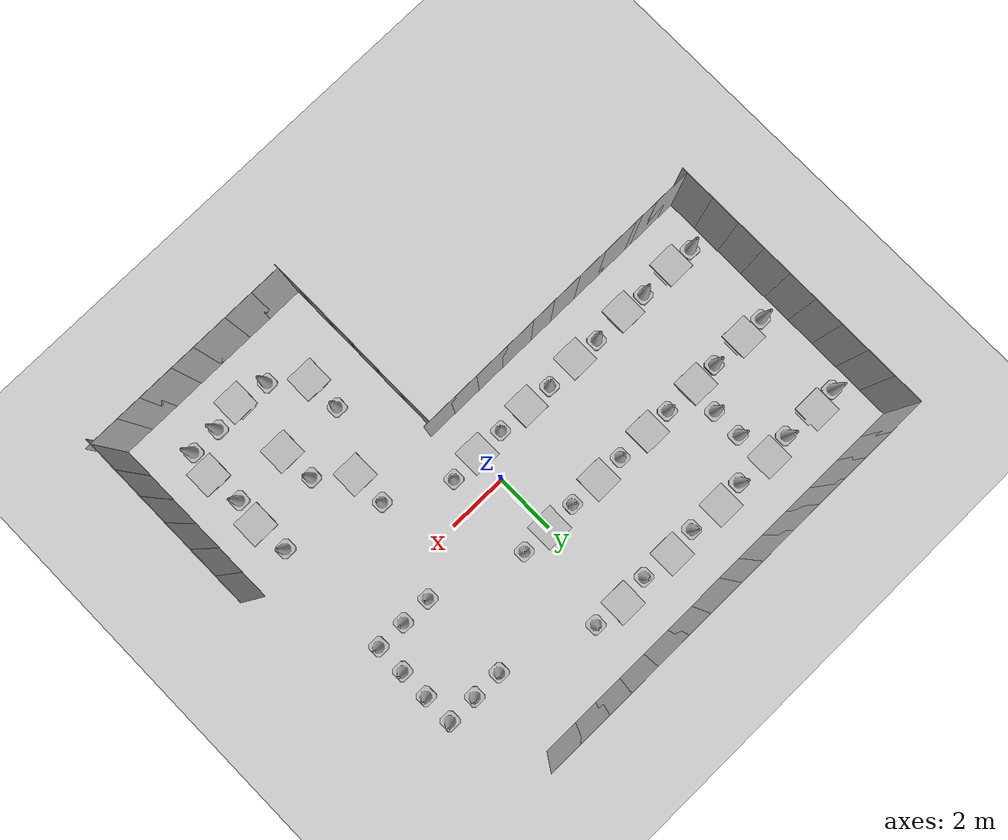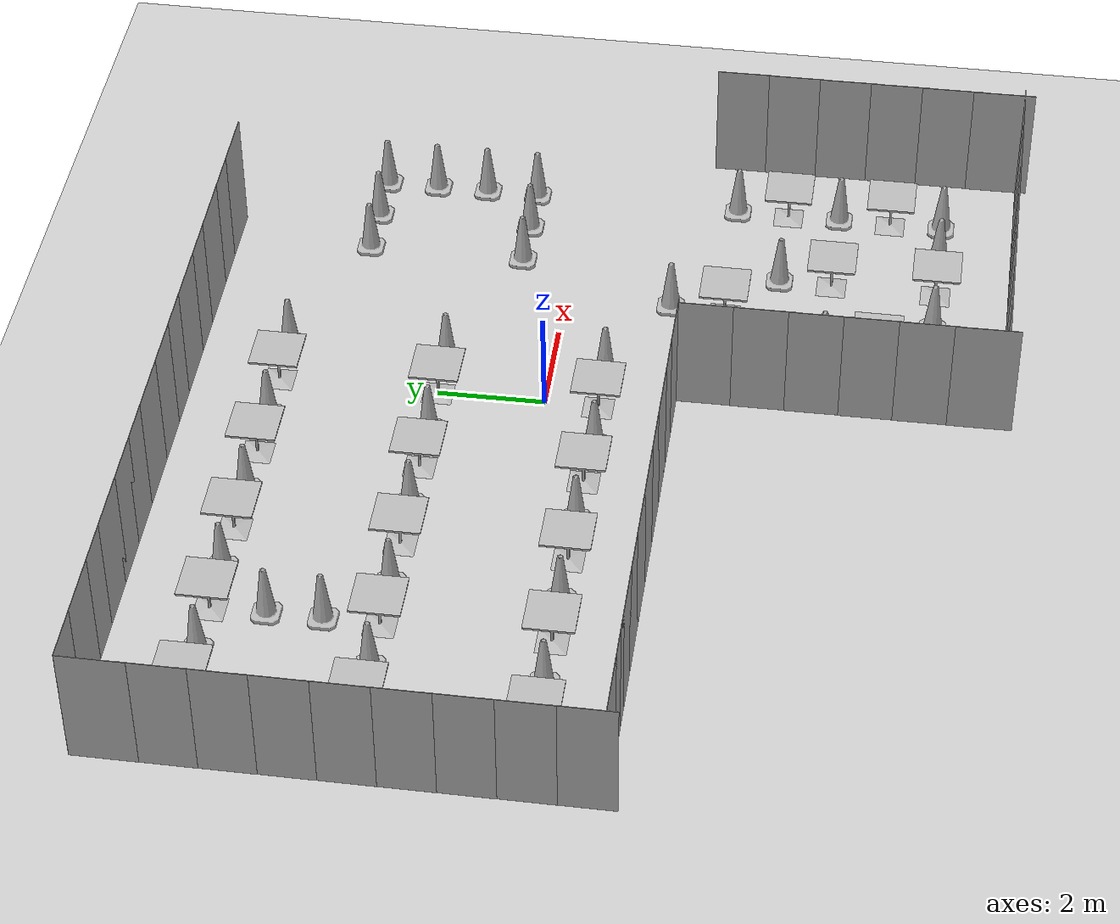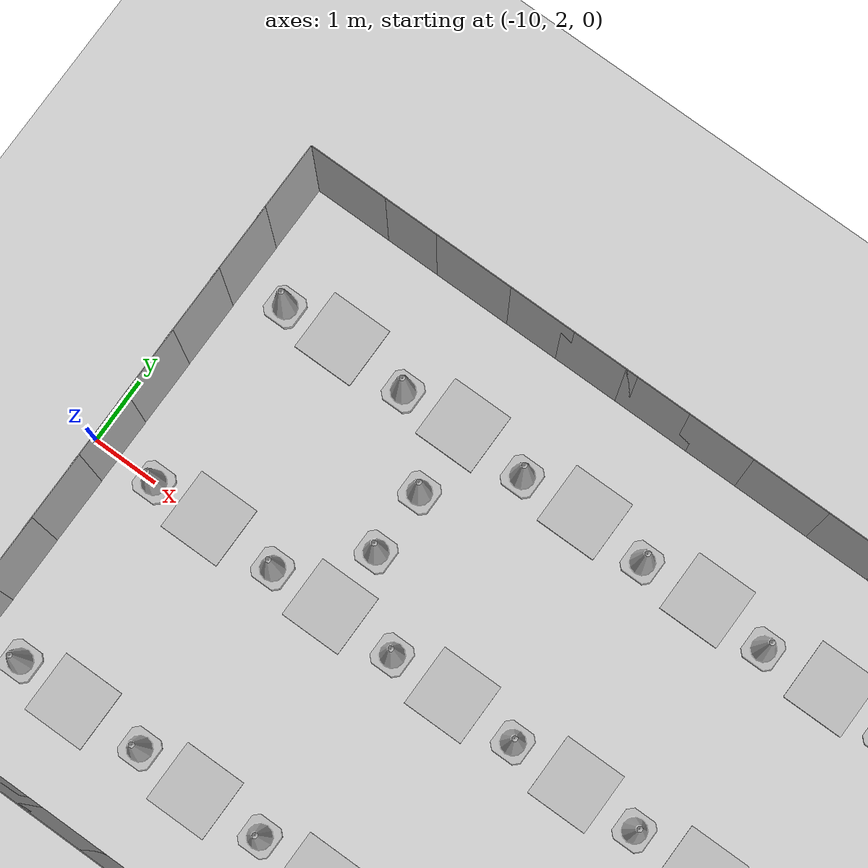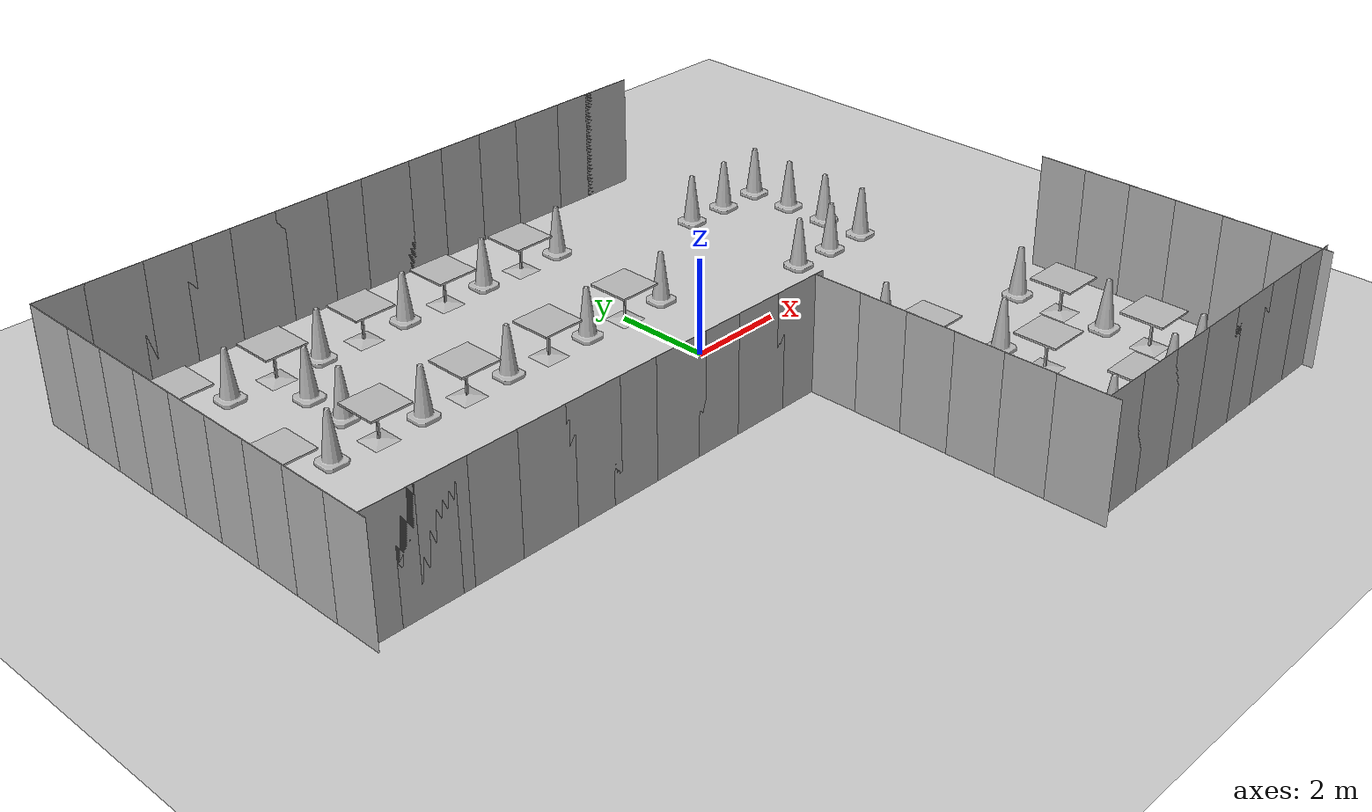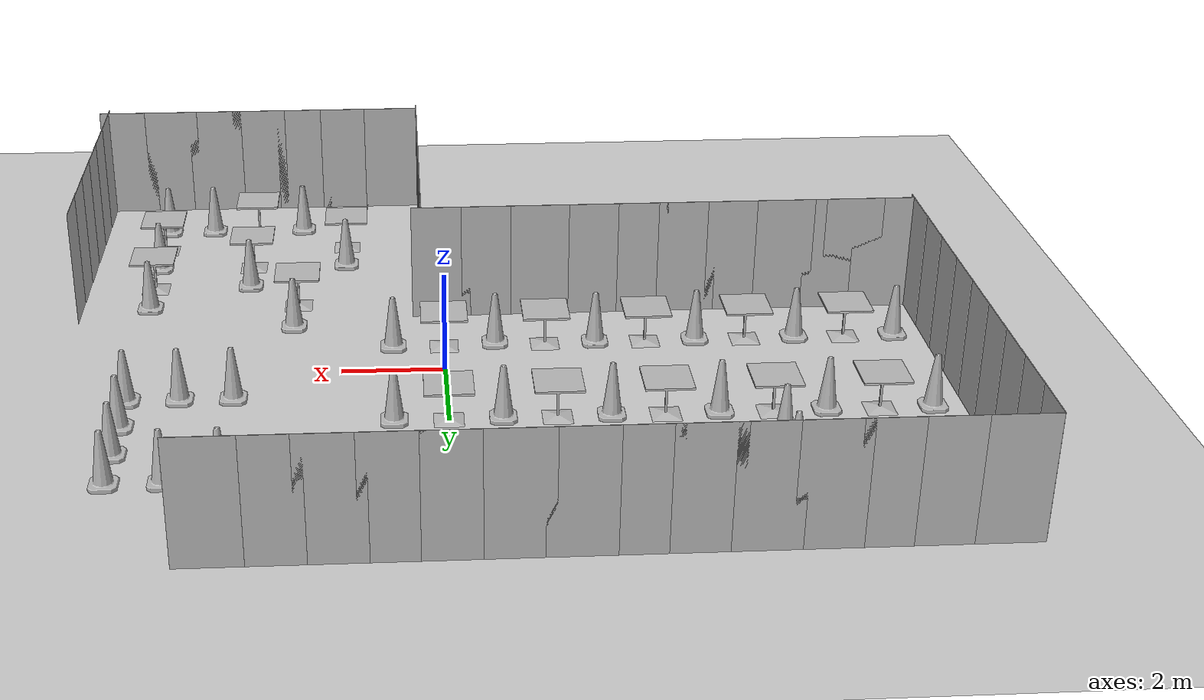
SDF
<sdf version="1.6">
 <world name="default">
  <light name="sun" type="directional">
   <pose>0 0 10 0 -0 0</pose>
   <diffuse>0.8 0.8 0.8 1</diffuse>
   <specular>0.2 0.2 0.2 1</specular>
   <attenuation>
    <range>1000</range>
    <constant>0.9</constant>
    <linear>0.01</linear>
    <quadratic>0.001</quadratic>
   </attenuation>
   <direction>-0.5 0.1 -0.9</direction>
  </light>
  <model name="ground_plane">
   <static>1</static>
   <link name="link">
    <collision name="collision">
     <geometry><plane><normal>0 0 1</normal><size>100 100</size></plane></geometry>
     <surface>
      <contact><collide_bitmask>65535</collide_bitmask></contact>
      <friction><ode><mu>100</mu><mu2>50</mu2></ode></friction>
     </surface>
    </collision>
    <visual name="visual">
     <cast_shadows>0</cast_shadows>
     <geometry><plane><normal>0 0 1</normal><size>100 100</size></plane></geometry>
     <material>
      <script><uri>file://media/materials/scripts/gazebo.material</uri><name>Gazebo/Grey</name></script>
     </material>
    </visual>
   </link>
  </model>
  <gravity>0 0 -9.8</gravity>
  <magnetic_field>6e-06 2.3e-05 -4.2e-05</magnetic_field>
  <atmosphere type="adiabatic"/>
  <physics name="default_physics" default="0" type="ode">
   <max_step_size>0.001</max_step_size>
   <real_time_factor>1</real_time_factor>
   <real_time_update_rate>1000</real_time_update_rate>
  </physics>
  <scene><ambient>0.4 0.4 0.4 1</ambient><background>0.7 0.7 0.7 1</background><shadows>1</shadows></scene>
  <spherical_coordinates>
   <surface_model>EARTH_WGS84</surface_model>
   <latitude_deg>0</latitude_deg>
   <longitude_deg>0</longitude_deg>
   <elevation>0</elevation>
   <heading_deg>0</heading_deg>
  </spherical_coordinates>
  <model name="cafe_table">
   <static>1</static>
   <link name="link">
    <collision name="surface">
     <pose>0 0 0.755 0 -0 0</pose>
     <geometry><box><size>0.913 0.913 0.04</size></box></geometry>
    </collision>
    <collision name="column">
     <pose>0 0 0.37 0 -0 0</pose>
     <geometry><box><size>0.042 0.042 0.74</size></box></geometry>
    </collision>
    <collision name="base">
     <pose>0 0 0.02 0 -0 0</pose>
     <geometry><box><size>0.56 0.56 0.04</size></box></geometry>
    </collision>
    <visual name="visual">
     <geometry><mesh><uri>model://cafe_table/meshes/cafe_table.dae</uri></mesh></geometry>
    </visual>
   </link>
   <pose>-4 -1 0 0 -0 0</pose>
  </model>
  <model name="cafe_table_clone">
   <static>1</static>
   <link name="link">
    <collision name="surface">
     <pose>0 0 0.755 0 -0 0</pose>
     <geometry><box><size>0.913 0.913 0.04</size></box></geometry>
    </collision>
    <collision name="column">
     <pose>0 0 0.37 0 -0 0</pose>
     <geometry><box><size>0.042 0.042 0.74</size></box></geometry>
    </collision>
    <collision name="base">
     <pose>0 0 0.02 0 -0 0</pose>
     <geometry><box><size>0.56 0.56 0.04</size></box></geometry>
    </collision>
    <visual name="visual">
     <geometry><mesh><uri>model://cafe_table/meshes/cafe_table.dae</uri></mesh></geometry>
    </visual>
   </link>
   <pose>-2 -1 0 0 -0 0</pose>
  </model>
  <model name="cafe_table_clone_0">
   <static>1</static>
   <link name="link">
    <collision name="surface">
     <pose>0 0 0.755 0 -0 0</pose>
     <geometry><box><size>0.913 0.913 0.04</size></box></geometry>
    </collision>
    <collision name="column">
     <pose>0 0 0.37 0 -0 0</pose>
     <geometry><box><size>0.042 0.042 0.74</size></box></geometry>
    </collision>
    <collision name="base">
     <pose>0 0 0.02 0 -0 0</pose>
     <geometry><box><size>0.56 0.56 0.04</size></box></geometry>
    </collision>
    <visual name="visual">
     <geometry><mesh><uri>model://cafe_table/meshes/cafe_table.dae</uri></mesh></geometry>
    </visual>
   </link>
   <pose>0 -1 0 0 -0 0</pose>
  </model>
  <model name="cafe_table_clone_1">
   <static>1</static>
   <link name="link">
    <collision name="surface">
     <pose>0 0 0.755 0 -0 0</pose>
     <geometry><box><size>0.913 0.913 0.04</size></box></geometry>
    </collision>
    <collision name="column">
     <pose>0 0 0.37 0 -0 0</pose>
     <geometry><box><size>0.042 0.042 0.74</size></box></geometry>
    </collision>
    <collision name="base">
     <pose>0 0 0.02 0 -0 0</pose>
     <geometry><box><size>0.56 0.56 0.04</size></box></geometry>
    </collision>
    <visual name="visual">
     <geometry><mesh><uri>model://cafe_table/meshes/cafe_table.dae</uri></mesh></geometry>
    </visual>
   </link>
   <pose>-6 -1 0 0 -0 0</pose>
  </model>
  <model name="cafe_table_clone_2">
   <static>1</static>
   <link name="link">
    <collision name="surface">
     <pose>0 0 0.755 0 -0 0</pose>
     <geometry><box><size>0.913 0.913 0.04</size></box></geometry>
    </collision>
    <collision name="column">
     <pose>0 0 0.37 0 -0 0</pose>
     <geometry><box><size>0.042 0.042 0.74</size></box></geometry>
    </collision>
    <collision name="base">
     <pose>0 0 0.02 0 -0 0</pose>
     <geometry><box><size>0.56 0.56 0.04</size></box></geometry>
    </collision>
    <visual name="visual">
     <geometry><mesh><uri>model://cafe_table/meshes/cafe_table.dae</uri></mesh></geometry>
    </visual>
   </link>
   <pose>-8 -1 0 0 -0 0</pose>
  </model>
  <model name="cafe_table_clone_3">
   <static>1</static>
   <link name="link">
    <collision name="surface">
     <pose>0 0 0.755 0 -0 0</pose>
     <geometry><box><size>0.913 0.913 0.04</size></box></geometry>
    </collision>
    <collision name="column">
     <pose>0 0 0.37 0 -0 0</pose>
     <geometry><box><size>0.042 0.042 0.74</size></box></geometry>
    </collision>
    <collision name="base">
     <pose>0 0 0.02 0 -0 0</pose>
     <geometry><box><size>0.56 0.56 0.04</size></box></geometry>
    </collision>
    <visual name="visual">
     <geometry><mesh><uri>model://cafe_table/meshes/cafe_table.dae</uri></mesh></geometry>
    </visual>
   </link>
   <pose>-8 2 0 0 -0 0</pose>
  </model>
  <model name="cafe_table_clone_4">
   <static>1</static>
   <link name="link">
    <collision name="surface">
     <pose>0 0 0.755 0 -0 0</pose>
     <geometry><box><size>0.913 0.913 0.04</size></box></geometry>
    </collision>
    <collision name="column">
     <pose>0 0 0.37 0 -0 0</pose>
     <geometry><box><size>0.042 0.042 0.74</size></box></geometry>
    </collision>
    <collision name="base">
     <pose>0 0 0.02 0 -0 0</pose>
     <geometry><box><size>0.56 0.56 0.04</size></box></geometry>
    </collision>
    <visual name="visual">
     <geometry><mesh><uri>model://cafe_table/meshes/cafe_table.dae</uri></mesh></geometry>
    </visual>
   </link>
   <pose>-6 2 0 0 -0 0</pose>
  </model>
  <model name="cafe_table_clone_5">
   <static>1</static>
   <link name="link">
    <collision name="surface">
     <pose>0 0 0.755 0 -0 0</pose>
     <geometry><box><size>0.913 0.913 0.04</size></box></geometry>
    </collision>
    <collision name="column">
     <pose>0 0 0.37 0 -0 0</pose>
     <geometry><box><size>0.042 0.042 0.74</size></box></geometry>
    </collision>
    <collision name="base">
     <pose>0 0 0.02 0 -0 0</pose>
     <geometry><box><size>0.56 0.56 0.04</size></box></geometry>
    </collision>
    <visual name="visual">
     <geometry><mesh><uri>model://cafe_table/meshes/cafe_table.dae</uri></mesh></geometry>
    </visual>
   </link>
   <pose>-4 2 0 0 -0 0</pose>
  </model>
  <model name="cafe_table_clone_6">
   <static>1</static>
   <link name="link">
    <collision name="surface">
     <pose>0 0 0.755 0 -0 0</pose>
     <geometry><box><size>0.913 0.913 0.04</size></box></geometry>
    </collision>
    <collision name="column">
     <pose>0 0 0.37 0 -0 0</pose>
     <geometry><box><size>0.042 0.042 0.74</size></box></geometry>
    </collision>
    <collision name="base">
     <pose>0 0 0.02 0 -0 0</pose>
     <geometry><box><size>0.56 0.56 0.04</size></box></geometry>
    </collision>
    <visual name="visual">
     <geometry><mesh><uri>model://cafe_table/meshes/cafe_table.dae</uri></mesh></geometry>
    </visual>
   </link>
   <pose>-2 2 0 0 -0 0</pose>
  </model>
  <model name="cafe_table_clone_7">
   <static>1</static>
   <link name="link">
    <collision name="surface">
     <pose>0 0 0.755 0 -0 0</pose>
     <geometry><box><size>0.913 0.913 0.04</size></box></geometry>
    </collision>
    <collision name="column">
     <pose>0 0 0.37 0 -0 0</pose>
     <geometry><box><size>0.042 0.042 0.74</size></box></geometry>
    </collision>
    <collision name="base">
     <pose>0 0 0.02 0 -0 0</pose>
     <geometry><box><size>0.56 0.56 0.04</size></box></geometry>
    </collision>
    <visual name="visual">
     <geometry><mesh><uri>model://cafe_table/meshes/cafe_table.dae</uri></mesh></geometry>
    </visual>
   </link>
   <pose>0 2 0 0 -0 0</pose>
  </model>
  <model name="cafe_table_clone_8">
   <static>1</static>
   <link name="link">
    <collision name="surface">
     <pose>0 0 0.755 0 -0 0</pose>
     <geometry><box><size>0.913 0.913 0.04</size></box></geometry>
    </collision>
    <collision name="column">
     <pose>0 0 0.37 0 -0 0</pose>
     <geometry><box><size>0.042 0.042 0.74</size></box></geometry>
    </collision>
    <collision name="base">
     <pose>0 0 0.02 0 -0 0</pose>
     <geometry><box><size>0.56 0.56 0.04</size></box></geometry>
    </collision>
    <visual name="visual">
     <geometry><mesh><uri>model://cafe_table/meshes/cafe_table.dae</uri></mesh></geometry>
    </visual>
   </link>
   <pose>-8 5 0 0 -0 0</pose>
  </model>
  <model name="cafe_table_clone_9">
   <static>1</static>
   <link name="link">
    <collision name="surface">
     <pose>0 0 0.755 0 -0 0</pose>
     <geometry><box><size>0.913 0.913 0.04</size></box></geometry>
    </collision>
    <collision name="column">
     <pose>0 0 0.37 0 -0 0</pose>
     <geometry><box><size>0.042 0.042 0.74</size></box></geometry>
    </collision>
    <collision name="base">
     <pose>0 0 0.02 0 -0 0</pose>
     <geometry><box><size>0.56 0.56 0.04</size></box></geometry>
    </collision>
    <visual name="visual">
     <geometry><mesh><uri>model://cafe_table/meshes/cafe_table.dae</uri></mesh></geometry>
    </visual>
   </link>
   <pose>-6 5 0 0 -0 0</pose>
  </model>
  <model name="cafe_table_clone_10">
   <static>1</static>
   <link name="link">
    <collision name="surface">
     <pose>0 0 0.755 0 -0 0</pose>
     <geometry><box><size>0.913 0.913 0.04</size></box></geometry>
    </collision>
    <collision name="column">
     <pose>0 0 0.37 0 -0 0</pose>
     <geometry><box><size>0.042 0.042 0.74</size></box></geometry>
    </collision>
    <collision name="base">
     <pose>0 0 0.02 0 -0 0</pose>
     <geometry><box><size>0.56 0.56 0.04</size></box></geometry>
    </collision>
    <visual name="visual">
     <geometry><mesh><uri>model://cafe_table/meshes/cafe_table.dae</uri></mesh></geometry>
    </visual>
   </link>
   <pose>-4 5 0 0 -0 0</pose>
  </model>
  <model name="cafe_table_clone_11">
   <static>1</static>
   <link name="link">
    <collision name="surface">
     <pose>0 0 0.755 0 -0 0</pose>
     <geometry><box><size>0.913 0.913 0.04</size></box></geometry>
    </collision>
    <collision name="column">
     <pose>0 0 0.37 0 -0 0</pose>
     <geometry><box><size>0.042 0.042 0.74</size></box></geometry>
    </collision>
    <collision name="base">
     <pose>0 0 0.02 0 -0 0</pose>
     <geometry><box><size>0.56 0.56 0.04</size></box></geometry>
    </collision>
    <visual name="visual">
     <geometry><mesh><uri>model://cafe_table/meshes/cafe_table.dae</uri></mesh></geometry>
    </visual>
   </link>
   <pose>-2 5 0 0 -0 0</pose>
  </model>
  <model name="cafe_table_clone_12">
   <static>1</static>
   <link name="link">
    <collision name="surface">
     <pose>0 0 0.755 0 -0 0</pose>
     <geometry><box><size>0.913 0.913 0.04</size></box></geometry>
    </collision>
    <collision name="column">
     <pose>0 0 0.37 0 -0 0</pose>
     <geometry><box><size>0.042 0.042 0.74</size></box></geometry>
    </collision>
    <collision name="base">
     <pose>0 0 0.02 0 -0 0</pose>
     <geometry><box><size>0.56 0.56 0.04</size></box></geometry>
    </collision>
    <visual name="visual">
     <geometry><mesh><uri>model://cafe_table/meshes/cafe_table.dae</uri></mesh></geometry>
    </visual>
   </link>
   <pose>0 5 0 0 -0 0</pose>
  </model>
  <model name="cafe_table_0">
   <static>1</static>
   <link name="link">
    <collision name="surface">
     <pose>0 0 0.755 0 -0 0</pose>
     <geometry><box><size>0.913 0.913 0.04</size></box></geometry>
    </collision>
    <collision name="column">
     <pose>0 0 0.37 0 -0 0</pose>
     <geometry><box><size>0.042 0.042 0.74</size></box></geometry>
    </collision>
    <collision name="base">
     <pose>0 0 0.02 0 -0 0</pose>
     <geometry><box><size>0.56 0.56 0.04</size></box></geometry>
    </collision>
    <visual name="visual">
     <geometry><mesh><uri>model://cafe_table/meshes/cafe_table.dae</uri></mesh></geometry>
    </visual>
   </link>
   <pose>2.95221 -3.03948 0 0 -0 0</pose>
  </model>
  <model name="cafe_table_0_clone">
   <static>1</static>
   <link name="link">
    <collision name="surface">
     <pose>0 0 0.755 0 -0 0</pose>
     <geometry><box><size>0.913 0.913 0.04</size></box></geometry>
    </collision>
    <collision name="column">
     <pose>0 0 0.37 0 -0 0</pose>
     <geometry><box><size>0.042 0.042 0.74</size></box></geometry>
    </collision>
    <collision name="base">
     <pose>0 0 0.02 0 -0 0</pose>
     <geometry><box><size>0.56 0.56 0.04</size></box></geometry>
    </collision>
    <visual name="visual">
     <geometry><mesh><uri>model://cafe_table/meshes/cafe_table.dae</uri></mesh></geometry>
    </visual>
   </link>
   <pose>4 -5 0 0 -0 0</pose>
  </model>
  <model name="cafe_table_0_clone_0">
   <static>1</static>
   <link name="link">
    <collision name="surface">
     <pose>0 0 0.755 0 -0 0</pose>
     <geometry><box><size>0.913 0.913 0.04</size></box></geometry>
    </collision>
    <collision name="column">
     <pose>0 0 0.37 0 -0 0</pose>
     <geometry><box><size>0.042 0.042 0.74</size></box></geometry>
    </collision>
    <collision name="base">
     <pose>0 0 0.02 0 -0 0</pose>
     <geometry><box><size>0.56 0.56 0.04</size></box></geometry>
    </collision>
    <visual name="visual">
     <geometry><mesh><uri>model://cafe_table/meshes/cafe_table.dae</uri></mesh></geometry>
    </visual>
   </link>
   <pose>6 -4 0 0 -0 0</pose>
  </model>
  <model name="cafe_table_0_clone_1">
   <static>1</static>
   <link name="link">
    <collision name="surface">
     <pose>0 0 0.755 0 -0 0</pose>
     <geometry><box><size>0.913 0.913 0.04</size></box></geometry>
    </collision>
    <collision name="column">
     <pose>0 0 0.37 0 -0 0</pose>
     <geometry><box><size>0.042 0.042 0.74</size></box></geometry>
    </collision>
    <collision name="base">
     <pose>0 0 0.02 0 -0 0</pose>
     <geometry><box><size>0.56 0.56 0.04</size></box></geometry>
    </collision>
    <visual name="visual">
     <geometry><mesh><uri>model://cafe_table/meshes/cafe_table.dae</uri></mesh></geometry>
    </visual>
   </link>
   <pose>2 -6 0 0 -0 0</pose>
  </model>
  <model name="cafe_table_0_clone_2">
   <static>1</static>
   <link name="link">
    <collision name="surface">
     <pose>0 0 0.755 0 -0 0</pose>
     <geometry><box><size>0.913 0.913 0.04</size></box></geometry>
    </collision>
    <collision name="column">
     <pose>0 0 0.37 0 -0 0</pose>
     <geometry><box><size>0.042 0.042 0.74</size></box></geometry>
    </collision>
    <collision name="base">
     <pose>0 0 0.02 0 -0 0</pose>
     <geometry><box><size>0.56 0.56 0.04</size></box></geometry>
    </collision>
    <visual name="visual">
     <geometry><mesh><uri>model://cafe_table/meshes/cafe_table.dae</uri></mesh></geometry>
    </visual>
   </link>
   <pose>4 -7 0 0 -0 0</pose>
  </model>
  <model name="cafe_table_0_clone_3">
   <static>1</static>
   <link name="link">
    <collision name="surface">
     <pose>0 0 0.755 0 -0 0</pose>
     <geometry><box><size>0.913 0.913 0.04</size></box></geometry>
    </collision>
    <collision name="column">
     <pose>0 0 0.37 0 -0 0</pose>
     <geometry><box><size>0.042 0.042 0.74</size></box></geometry>
    </collision>
    <collision name="base">
     <pose>0 0 0.02 0 -0 0</pose>
     <geometry><box><size>0.56 0.56 0.04</size></box></geometry>
    </collision>
    <visual name="visual">
     <geometry><mesh><uri>model://cafe_table/meshes/cafe_table.dae</uri></mesh></geometry>
    </visual>
   </link>
   <pose>6 -6 0 0 -0 0</pose>
  </model>
  <model name="nist_maze_wall_240">
   <static>1</static>
   <link name="nist__maze_wall_240_link">
    <collision name="collision">
     <geometry>
      <mesh><uri>model://nist_maze_wall_240/meshes/nist_maze_wall_240.dae</uri><scale>1 1 1</scale></mesh>
     </geometry>
    </collision>
    <visual name="visual">
     <geometry>
      <mesh><uri>model://nist_maze_wall_240/meshes/nist_maze_wall_240.dae</uri><scale>1 1 1</scale></mesh>
     </geometry>
    </visual>
   </link>
   <pose>0 -3 0 0 -0 0</pose>
  </model>
  <model name="nist_maze_wall_240_clone">
   <static>1</static>
   <link name="nist__maze_wall_240_link">
    <collision name="collision">
     <geometry>
      <mesh><uri>model://nist_maze_wall_240/meshes/nist_maze_wall_240.dae</uri><scale>1 1 1</scale></mesh>
     </geometry>
    </collision>
    <visual name="visual">
     <geometry>
      <mesh><uri>model://nist_maze_wall_240/meshes/nist_maze_wall_240.dae</uri><scale>1 1 1</scale></mesh>
     </geometry>
    </visual>
   </link>
   <pose>-1 -3 0 0 -0 0</pose>
  </model>
  <model name="nist_maze_wall_240_clone_0">
   <static>1</static>
   <link name="nist__maze_wall_240_link">
    <collision name="collision">
     <geometry>
      <mesh><uri>model://nist_maze_wall_240/meshes/nist_maze_wall_240.dae</uri><scale>1 1 1</scale></mesh>
     </geometry>
    </collision>
    <visual name="visual">
     <geometry>
      <mesh><uri>model://nist_maze_wall_240/meshes/nist_maze_wall_240.dae</uri><scale>1 1 1</scale></mesh>
     </geometry>
    </visual>
   </link>
   <pose>-2 -3 0 0 -0 0</pose>
  </model>
  <model name="nist_maze_wall_240_clone_1">
   <static>1</static>
   <link name="nist__maze_wall_240_link">
    <collision name="collision">
     <geometry>
      <mesh><uri>model://nist_maze_wall_240/meshes/nist_maze_wall_240.dae</uri><scale>1 1 1</scale></mesh>
     </geometry>
    </collision>
    <visual name="visual">
     <geometry>
      <mesh><uri>model://nist_maze_wall_240/meshes/nist_maze_wall_240.dae</uri><scale>1 1 1</scale></mesh>
     </geometry>
    </visual>
   </link>
   <pose>-3 -3 0 0 -0 0</pose>
  </model>
  <model name="nist_maze_wall_240_clone_2">
   <static>1</static>
   <link name="nist__maze_wall_240_link">
    <collision name="collision">
     <geometry>
      <mesh><uri>model://nist_maze_wall_240/meshes/nist_maze_wall_240.dae</uri><scale>1 1 1</scale></mesh>
     </geometry>
    </collision>
    <visual name="visual">
     <geometry>
      <mesh><uri>model://nist_maze_wall_240/meshes/nist_maze_wall_240.dae</uri><scale>1 1 1</scale></mesh>
     </geometry>
    </visual>
   </link>
   <pose>-4 -3 0 0 -0 0</pose>
  </model>
  <model name="nist_maze_wall_240_clone_3">
   <static>1</static>
   <link name="nist__maze_wall_240_link">
    <collision name="collision">
     <geometry>
      <mesh><uri>model://nist_maze_wall_240/meshes/nist_maze_wall_240.dae</uri><scale>1 1 1</scale></mesh>
     </geometry>
    </collision>
    <visual name="visual">
     <geometry>
      <mesh><uri>model://nist_maze_wall_240/meshes/nist_maze_wall_240.dae</uri><scale>1 1 1</scale></mesh>
     </geometry>
    </visual>
   </link>
   <pose>-5 -3 0 0 -0 0</pose>
  </model>
  <model name="nist_maze_wall_240_clone_4">
   <static>1</static>
   <link name="nist__maze_wall_240_link">
    <collision name="collision">
     <geometry>
      <mesh><uri>model://nist_maze_wall_240/meshes/nist_maze_wall_240.dae</uri><scale>1 1 1</scale></mesh>
     </geometry>
    </collision>
    <visual name="visual">
     <geometry>
      <mesh><uri>model://nist_maze_wall_240/meshes/nist_maze_wall_240.dae</uri><scale>1 1 1</scale></mesh>
     </geometry>
    </visual>
   </link>
   <pose>-6 -3 0 0 -0 0</pose>
  </model>
  <model name="nist_maze_wall_240_clone_5">
   <static>1</static>
   <link name="nist__maze_wall_240_link">
    <collision name="collision">
     <geometry>
      <mesh><uri>model://nist_maze_wall_240/meshes/nist_maze_wall_240.dae</uri><scale>1 1 1</scale></mesh>
     </geometry>
    </collision>
    <visual name="visual">
     <geometry>
      <mesh><uri>model://nist_maze_wall_240/meshes/nist_maze_wall_240.dae</uri><scale>1 1 1</scale></mesh>
     </geometry>
    </visual>
   </link>
   <pose>-7 -3 0 0 -0 0</pose>
  </model>
  <model name="nist_maze_wall_240_clone_6">
   <static>1</static>
   <link name="nist__maze_wall_240_link">
    <collision name="collision">
     <geometry>
      <mesh><uri>model://nist_maze_wall_240/meshes/nist_maze_wall_240.dae</uri><scale>1 1 1</scale></mesh>
     </geometry>
    </collision>
    <visual name="visual">
     <geometry>
      <mesh><uri>model://nist_maze_wall_240/meshes/nist_maze_wall_240.dae</uri><scale>1 1 1</scale></mesh>
     </geometry>
    </visual>
   </link>
   <pose>-8.41484 -3 0 0 -0 0</pose>
  </model>
  <model name="nist_maze_wall_240_clone_7">
   <static>1</static>
   <link name="nist__maze_wall_240_link">
    <collision name="collision">
     <geometry>
      <mesh><uri>model://nist_maze_wall_240/meshes/nist_maze_wall_240.dae</uri><scale>1 1 1</scale></mesh>
     </geometry>
    </collision>
    <visual name="visual">
     <geometry>
      <mesh><uri>model://nist_maze_wall_240/meshes/nist_maze_wall_240.dae</uri><scale>1 1 1</scale></mesh>
     </geometry>
    </visual>
   </link>
   <pose>-8 -3 0 0 -0 0</pose>
  </model>
  <model name="nist_maze_wall_240_clone_8">
   <static>1</static>
   <link name="nist__maze_wall_240_link">
    <collision name="collision">
     <geometry>
      <mesh><uri>model://nist_maze_wall_240/meshes/nist_maze_wall_240.dae</uri><scale>1 1 1</scale></mesh>
     </geometry>
    </collision>
    <visual name="visual">
     <geometry>
      <mesh><uri>model://nist_maze_wall_240/meshes/nist_maze_wall_240.dae</uri><scale>1 1 1</scale></mesh>
     </geometry>
    </visual>
   </link>
   <pose>-9 -3 0 0 -0 0</pose>
  </model>
  <model name="nist_maze_wall_240_clone_9_clone">
   <static>1</static>
   <link name="nist__maze_wall_240_link">
    <collision name="collision">
     <geometry>
      <mesh><uri>model://nist_maze_wall_240/meshes/nist_maze_wall_240.dae</uri><scale>1 1 1</scale></mesh>
     </geometry>
    </collision>
    <visual name="visual">
     <geometry>
      <mesh><uri>model://nist_maze_wall_240/meshes/nist_maze_wall_240.dae</uri><scale>1 1 1</scale></mesh>
     </geometry>
    </visual>
   </link>
   <pose>-9 -2 0 0 -0 1.56666</pose>
  </model>
  <model name="nist_maze_wall_240_clone_9_clone_0">
   <static>1</static>
   <link name="nist__maze_wall_240_link">
    <collision name="collision">
     <geometry>
      <mesh><uri>model://nist_maze_wall_240/meshes/nist_maze_wall_240.dae</uri><scale>1 1 1</scale></mesh>
     </geometry>
    </collision>
    <visual name="visual">
     <geometry>
      <mesh><uri>model://nist_maze_wall_240/meshes/nist_maze_wall_240.dae</uri><scale>1 1 1</scale></mesh>
     </geometry>
    </visual>
   </link>
   <pose>-9 -1 0 0 -0 1.56666</pose>
  </model>
  <model name="nist_maze_wall_240_clone_9_clone_1">
   <static>1</static>
   <link name="nist__maze_wall_240_link">
    <collision name="collision">
     <geometry>
      <mesh><uri>model://nist_maze_wall_240/meshes/nist_maze_wall_240.dae</uri><scale>1 1 1</scale></mesh>
     </geometry>
    </collision>
    <visual name="visual">
     <geometry>
      <mesh><uri>model://nist_maze_wall_240/meshes/nist_maze_wall_240.dae</uri><scale>1 1 1</scale></mesh>
     </geometry>
    </visual>
   </link>
   <pose>-9 0 0 0 -0 1.56666</pose>
  </model>
  <model name="nist_maze_wall_240_clone_9_clone_2">
   <static>1</static>
   <link name="nist__maze_wall_240_link">
    <collision name="collision">
     <geometry>
      <mesh><uri>model://nist_maze_wall_240/meshes/nist_maze_wall_240.dae</uri><scale>1 1 1</scale></mesh>
     </geometry>
    </collision>
    <visual name="visual">
     <geometry>
      <mesh><uri>model://nist_maze_wall_240/meshes/nist_maze_wall_240.dae</uri><scale>1 1 1</scale></mesh>
     </geometry>
    </visual>
   </link>
   <pose>-9 1 0 0 -0 1.56666</pose>
  </model>
  <model name="nist_maze_wall_240_clone_9_clone_3">
   <static>1</static>
   <link name="nist__maze_wall_240_link">
    <collision name="collision">
     <geometry>
      <mesh><uri>model://nist_maze_wall_240/meshes/nist_maze_wall_240.dae</uri><scale>1 1 1</scale></mesh>
     </geometry>
    </collision>
    <visual name="visual">
     <geometry>
      <mesh><uri>model://nist_maze_wall_240/meshes/nist_maze_wall_240.dae</uri><scale>1 1 1</scale></mesh>
     </geometry>
    </visual>
   </link>
   <pose>-9 2 0 0 -0 1.56666</pose>
  </model>
  <model name="nist_maze_wall_240_clone_9_clone_4">
   <static>1</static>
   <link name="nist__maze_wall_240_link">
    <collision name="collision">
     <geometry>
      <mesh><uri>model://nist_maze_wall_240/meshes/nist_maze_wall_240.dae</uri><scale>1 1 1</scale></mesh>
     </geometry>
    </collision>
    <visual name="visual">
     <geometry>
      <mesh><uri>model://nist_maze_wall_240/meshes/nist_maze_wall_240.dae</uri><scale>1 1 1</scale></mesh>
     </geometry>
    </visual>
   </link>
   <pose>-9 3 0 0 -0 1.56666</pose>
  </model>
  <model name="nist_maze_wall_240_clone_9_clone_5">
   <static>1</static>
   <link name="nist__maze_wall_240_link">
    <collision name="collision">
     <geometry>
      <mesh><uri>model://nist_maze_wall_240/meshes/nist_maze_wall_240.dae</uri><scale>1 1 1</scale></mesh>
     </geometry>
    </collision>
    <visual name="visual">
     <geometry>
      <mesh><uri>model://nist_maze_wall_240/meshes/nist_maze_wall_240.dae</uri><scale>1 1 1</scale></mesh>
     </geometry>
    </visual>
   </link>
   <pose>-9 4 0 0 -0 1.56666</pose>
  </model>
  <model name="nist_maze_wall_240_clone_9_clone_6">
   <static>1</static>
   <link name="nist__maze_wall_240_link">
    <collision name="collision">
     <geometry>
      <mesh><uri>model://nist_maze_wall_240/meshes/nist_maze_wall_240.dae</uri><scale>1 1 1</scale></mesh>
     </geometry>
    </collision>
    <visual name="visual">
     <geometry>
      <mesh><uri>model://nist_maze_wall_240/meshes/nist_maze_wall_240.dae</uri><scale>1 1 1</scale></mesh>
     </geometry>
    </visual>
   </link>
   <pose>-9 5 0 0 -0 1.56666</pose>
  </model>
  <model name="nist_maze_wall_240_clone_9_clone_7">
   <static>1</static>
   <link name="nist__maze_wall_240_link">
    <collision name="collision">
     <geometry>
      <mesh><uri>model://nist_maze_wall_240/meshes/nist_maze_wall_240.dae</uri><scale>1 1 1</scale></mesh>
     </geometry>
    </collision>
    <visual name="visual">
     <geometry>
      <mesh><uri>model://nist_maze_wall_240/meshes/nist_maze_wall_240.dae</uri><scale>1 1 1</scale></mesh>
     </geometry>
    </visual>
   </link>
   <pose>-9 6 0 0 -0 1.56666</pose>
  </model>
  <model name="nist_maze_wall_240_clone_8_clone">
   <static>1</static>
   <link name="nist__maze_wall_240_link">
    <collision name="collision">
     <geometry>
      <mesh><uri>model://nist_maze_wall_240/meshes/nist_maze_wall_240.dae</uri><scale>1 1 1</scale></mesh>
     </geometry>
    </collision>
    <visual name="visual">
     <geometry>
      <mesh><uri>model://nist_maze_wall_240/meshes/nist_maze_wall_240.dae</uri><scale>1 1 1</scale></mesh>
     </geometry>
    </visual>
   </link>
   <pose>-9 6 0 0 -0 0</pose>
  </model>
  <model name="nist_maze_wall_240_clone_8_clone_0">
   <static>1</static>
   <link name="nist__maze_wall_240_link">
    <collision name="collision">
     <geometry>
      <mesh><uri>model://nist_maze_wall_240/meshes/nist_maze_wall_240.dae</uri><scale>1 1 1</scale></mesh>
     </geometry>
    </collision>
    <visual name="visual">
     <geometry>
      <mesh><uri>model://nist_maze_wall_240/meshes/nist_maze_wall_240.dae</uri><scale>1 1 1</scale></mesh>
     </geometry>
    </visual>
   </link>
   <pose>-8 6 0 0 -0 0</pose>
  </model>
  <model name="nist_maze_wall_240_clone_8_clone_1">
   <static>1</static>
   <link name="nist__maze_wall_240_link">
    <collision name="collision">
     <geometry>
      <mesh><uri>model://nist_maze_wall_240/meshes/nist_maze_wall_240.dae</uri><scale>1 1 1</scale></mesh>
     </geometry>
    </collision>
    <visual name="visual">
     <geometry>
      <mesh><uri>model://nist_maze_wall_240/meshes/nist_maze_wall_240.dae</uri><scale>1 1 1</scale></mesh>
     </geometry>
    </visual>
   </link>
   <pose>-7 6 0 0 -0 0</pose>
  </model>
  <model name="nist_maze_wall_240_clone_8_clone_2">
   <static>1</static>
   <link name="nist__maze_wall_240_link">
    <collision name="collision">
     <geometry>
      <mesh><uri>model://nist_maze_wall_240/meshes/nist_maze_wall_240.dae</uri><scale>1 1 1</scale></mesh>
     </geometry>
    </collision>
    <visual name="visual">
     <geometry>
      <mesh><uri>model://nist_maze_wall_240/meshes/nist_maze_wall_240.dae</uri><scale>1 1 1</scale></mesh>
     </geometry>
    </visual>
   </link>
   <pose>-6 6 0 0 -0 0</pose>
  </model>
  <model name="nist_maze_wall_240_clone_8_clone_3">
   <static>1</static>
   <link name="nist__maze_wall_240_link">
    <collision name="collision">
     <geometry>
      <mesh><uri>model://nist_maze_wall_240/meshes/nist_maze_wall_240.dae</uri><scale>1 1 1</scale></mesh>
     </geometry>
    </collision>
    <visual name="visual">
     <geometry>
      <mesh><uri>model://nist_maze_wall_240/meshes/nist_maze_wall_240.dae</uri><scale>1 1 1</scale></mesh>
     </geometry>
    </visual>
   </link>
   <pose>-5 6 0 0 -0 0</pose>
  </model>
  <model name="nist_maze_wall_240_clone_8_clone_4">
   <static>1</static>
   <link name="nist__maze_wall_240_link">
    <collision name="collision">
     <geometry>
      <mesh><uri>model://nist_maze_wall_240/meshes/nist_maze_wall_240.dae</uri><scale>1 1 1</scale></mesh>
     </geometry>
    </collision>
    <visual name="visual">
     <geometry>
      <mesh><uri>model://nist_maze_wall_240/meshes/nist_maze_wall_240.dae</uri><scale>1 1 1</scale></mesh>
     </geometry>
    </visual>
   </link>
   <pose>-4 6 0 0 -0 0</pose>
  </model>
  <model name="nist_maze_wall_240_clone_8_clone_5">
   <static>1</static>
   <link name="nist__maze_wall_240_link">
    <collision name="collision">
     <geometry>
      <mesh><uri>model://nist_maze_wall_240/meshes/nist_maze_wall_240.dae</uri><scale>1 1 1</scale></mesh>
     </geometry>
    </collision>
    <visual name="visual">
     <geometry>
      <mesh><uri>model://nist_maze_wall_240/meshes/nist_maze_wall_240.dae</uri><scale>1 1 1</scale></mesh>
     </geometry>
    </visual>
   </link>
   <pose>-3 6 0 0 -0 0</pose>
  </model>
  <model name="nist_maze_wall_240_clone_8_clone_6">
   <static>1</static>
   <link name="nist__maze_wall_240_link">
    <collision name="collision">
     <geometry>
      <mesh><uri>model://nist_maze_wall_240/meshes/nist_maze_wall_240.dae</uri><scale>1 1 1</scale></mesh>
     </geometry>
    </collision>
    <visual name="visual">
     <geometry>
      <mesh><uri>model://nist_maze_wall_240/meshes/nist_maze_wall_240.dae</uri><scale>1 1 1</scale></mesh>
     </geometry>
    </visual>
   </link>
   <pose>-2 6 0 0 -0 0</pose>
  </model>
  <model name="nist_maze_wall_240_clone_8_clone_7">
   <static>1</static>
   <link name="nist__maze_wall_240_link">
    <collision name="collision">
     <geometry>
      <mesh><uri>model://nist_maze_wall_240/meshes/nist_maze_wall_240.dae</uri><scale>1 1 1</scale></mesh>
     </geometry>
    </collision>
    <visual name="visual">
     <geometry>
      <mesh><uri>model://nist_maze_wall_240/meshes/nist_maze_wall_240.dae</uri><scale>1 1 1</scale></mesh>
     </geometry>
    </visual>
   </link>
   <pose>-1 6 0 0 -0 0</pose>
  </model>
  <model name="nist_maze_wall_240_clone_8_clone_8">
   <static>1</static>
   <link name="nist__maze_wall_240_link">
    <collision name="collision">
     <geometry>
      <mesh><uri>model://nist_maze_wall_240/meshes/nist_maze_wall_240.dae</uri><scale>1 1 1</scale></mesh>
     </geometry>
    </collision>
    <visual name="visual">
     <geometry>
      <mesh><uri>model://nist_maze_wall_240/meshes/nist_maze_wall_240.dae</uri><scale>1 1 1</scale></mesh>
     </geometry>
    </visual>
   </link>
   <pose>0 6 0 0 -0 0</pose>
  </model>
  <model name="nist_maze_wall_240_clone_8_clone_9">
   <static>1</static>
   <link name="nist__maze_wall_240_link">
    <collision name="collision">
     <geometry>
      <mesh><uri>model://nist_maze_wall_240/meshes/nist_maze_wall_240.dae</uri><scale>1 1 1</scale></mesh>
     </geometry>
    </collision>
    <visual name="visual">
     <geometry>
      <mesh><uri>model://nist_maze_wall_240/meshes/nist_maze_wall_240.dae</uri><scale>1 1 1</scale></mesh>
     </geometry>
    </visual>
   </link>
   <pose>1 6 0 0 -0 0</pose>
  </model>
  <model name="nist_maze_wall_240_clone_8_clone_10">
   <static>1</static>
   <link name="nist__maze_wall_240_link">
    <collision name="collision">
     <geometry>
      <mesh><uri>model://nist_maze_wall_240/meshes/nist_maze_wall_240.dae</uri><scale>1 1 1</scale></mesh>
     </geometry>
    </collision>
    <visual name="visual">
     <geometry>
      <mesh><uri>model://nist_maze_wall_240/meshes/nist_maze_wall_240.dae</uri><scale>1 1 1</scale></mesh>
     </geometry>
    </visual>
   </link>
   <pose>2 6 0 0 -0 0</pose>
  </model>
  <model name="nist_maze_wall_240_clone_8_clone_11">
   <static>1</static>
   <link name="nist__maze_wall_240_link">
    <collision name="collision">
     <geometry>
      <mesh><uri>model://nist_maze_wall_240/meshes/nist_maze_wall_240.dae</uri><scale>1 1 1</scale></mesh>
     </geometry>
    </collision>
    <visual name="visual">
     <geometry>
      <mesh><uri>model://nist_maze_wall_240/meshes/nist_maze_wall_240.dae</uri><scale>1 1 1</scale></mesh>
     </geometry>
    </visual>
   </link>
   <pose>3 6 0 0 -0 0</pose>
  </model>
  <model name="nist_maze_wall_240_clone_8_clone_12">
   <static>1</static>
   <link name="nist__maze_wall_240_link">
    <collision name="collision">
     <geometry>
      <mesh><uri>model://nist_maze_wall_240/meshes/nist_maze_wall_240.dae</uri><scale>1 1 1</scale></mesh>
     </geometry>
    </collision>
    <visual name="visual">
     <geometry>
      <mesh><uri>model://nist_maze_wall_240/meshes/nist_maze_wall_240.dae</uri><scale>1 1 1</scale></mesh>
     </geometry>
    </visual>
   </link>
   <pose>4 6 0 0 -0 0</pose>
  </model>
  <model name="nist_maze_wall_240_clone_8_clone_13_clone">
   <static>1</static>
   <link name="nist__maze_wall_240_link">
    <collision name="collision">
     <geometry>
      <mesh><uri>model://nist_maze_wall_240/meshes/nist_maze_wall_240.dae</uri><scale>1 1 1</scale></mesh>
     </geometry>
    </collision>
    <visual name="visual">
     <geometry>
      <mesh><uri>model://nist_maze_wall_240/meshes/nist_maze_wall_240.dae</uri><scale>1 1 1</scale></mesh>
     </geometry>
    </visual>
   </link>
   <pose>1 -3 0 0 -0 1.57853</pose>
  </model>
  <model name="nist_maze_wall_240_clone_8_clone_13_clone_0">
   <static>1</static>
   <link name="nist__maze_wall_240_link">
    <collision name="collision">
     <geometry>
      <mesh><uri>model://nist_maze_wall_240/meshes/nist_maze_wall_240.dae</uri><scale>1 1 1</scale></mesh>
     </geometry>
    </collision>
    <visual name="visual">
     <geometry>
      <mesh><uri>model://nist_maze_wall_240/meshes/nist_maze_wall_240.dae</uri><scale>1 1 1</scale></mesh>
     </geometry>
    </visual>
   </link>
   <pose>1 -4 0 0 -0 1.57853</pose>
  </model>
  <model name="nist_maze_wall_240_clone_8_clone_13_clone_1">
   <static>1</static>
   <link name="nist__maze_wall_240_link">
    <collision name="collision">
     <geometry>
      <mesh><uri>model://nist_maze_wall_240/meshes/nist_maze_wall_240.dae</uri><scale>1 1 1</scale></mesh>
     </geometry>
    </collision>
    <visual name="visual">
     <geometry>
      <mesh><uri>model://nist_maze_wall_240/meshes/nist_maze_wall_240.dae</uri><scale>1 1 1</scale></mesh>
     </geometry>
    </visual>
   </link>
   <pose>1 -5 0 0 -0 1.57853</pose>
  </model>
  <model name="nist_maze_wall_240_clone_8_clone_13_clone_2">
   <static>1</static>
   <link name="nist__maze_wall_240_link">
    <collision name="collision">
     <geometry>
      <mesh><uri>model://nist_maze_wall_240/meshes/nist_maze_wall_240.dae</uri><scale>1 1 1</scale></mesh>
     </geometry>
    </collision>
    <visual name="visual">
     <geometry>
      <mesh><uri>model://nist_maze_wall_240/meshes/nist_maze_wall_240.dae</uri><scale>1 1 1</scale></mesh>
     </geometry>
    </visual>
   </link>
   <pose>1 -6 0 0 -0 1.57853</pose>
  </model>
  <model name="nist_maze_wall_240_clone_8_clone_13_clone_3">
   <static>1</static>
   <link name="nist__maze_wall_240_link">
    <collision name="collision">
     <geometry>
      <mesh><uri>model://nist_maze_wall_240/meshes/nist_maze_wall_240.dae</uri><scale>1 1 1</scale></mesh>
     </geometry>
    </collision>
    <visual name="visual">
     <geometry>
      <mesh><uri>model://nist_maze_wall_240/meshes/nist_maze_wall_240.dae</uri><scale>1 1 1</scale></mesh>
     </geometry>
    </visual>
   </link>
   <pose>1 -7 0 0 -0 1.57853</pose>
  </model>
  <model name="nist_maze_wall_240_clone_8_clone_13_clone_4">
   <static>1</static>
   <link name="nist__maze_wall_240_link">
    <collision name="collision">
     <geometry>
      <mesh><uri>model://nist_maze_wall_240/meshes/nist_maze_wall_240.dae</uri><scale>1 1 1</scale></mesh>
     </geometry>
    </collision>
    <visual name="visual">
     <geometry>
      <mesh><uri>model://nist_maze_wall_240/meshes/nist_maze_wall_240.dae</uri><scale>1 1 1</scale></mesh>
     </geometry>
    </visual>
   </link>
   <pose>1 -8 0 0 -0 1.57853</pose>
  </model>
  <model name="nist_maze_wall_240_clone_8_clone_13_clone_5">
   <static>1</static>
   <link name="nist__maze_wall_240_link">
    <collision name="collision">
     <geometry>
      <mesh><uri>model://nist_maze_wall_240/meshes/nist_maze_wall_240.dae</uri><scale>1 1 1</scale></mesh>
     </geometry>
    </collision>
    <visual name="visual">
     <geometry>
      <mesh><uri>model://nist_maze_wall_240/meshes/nist_maze_wall_240.dae</uri><scale>1 1 1</scale></mesh>
     </geometry>
    </visual>
   </link>
   <pose>8 -3 0 0 -0 1.57853</pose>
  </model>
  <model name="nist_maze_wall_240_clone_8_clone_13_clone_6">
   <static>1</static>
   <link name="nist__maze_wall_240_link">
    <collision name="collision">
     <geometry>
      <mesh><uri>model://nist_maze_wall_240/meshes/nist_maze_wall_240.dae</uri><scale>1 1 1</scale></mesh>
     </geometry>
    </collision>
    <visual name="visual">
     <geometry>
      <mesh><uri>model://nist_maze_wall_240/meshes/nist_maze_wall_240.dae</uri><scale>1 1 1</scale></mesh>
     </geometry>
    </visual>
   </link>
   <pose>8 -4 0 0 -0 1.57853</pose>
  </model>
  <model name="nist_maze_wall_240_clone_8_clone_13_clone_7">
   <static>1</static>
   <link name="nist__maze_wall_240_link">
    <collision name="collision">
     <geometry>
      <mesh><uri>model://nist_maze_wall_240/meshes/nist_maze_wall_240.dae</uri><scale>1 1 1</scale></mesh>
     </geometry>
    </collision>
    <visual name="visual">
     <geometry>
      <mesh><uri>model://nist_maze_wall_240/meshes/nist_maze_wall_240.dae</uri><scale>1 1 1</scale></mesh>
     </geometry>
    </visual>
   </link>
   <pose>8 -5 0 0 -0 1.57853</pose>
  </model>
  <model name="nist_maze_wall_240_clone_8_clone_13_clone_8">
   <static>1</static>
   <link name="nist__maze_wall_240_link">
    <collision name="collision">
     <geometry>
      <mesh><uri>model://nist_maze_wall_240/meshes/nist_maze_wall_240.dae</uri><scale>1 1 1</scale></mesh>
     </geometry>
    </collision>
    <visual name="visual">
     <geometry>
      <mesh><uri>model://nist_maze_wall_240/meshes/nist_maze_wall_240.dae</uri><scale>1 1 1</scale></mesh>
     </geometry>
    </visual>
   </link>
   <pose>8 -6 0 0 -0 1.57853</pose>
  </model>
  <model name="nist_maze_wall_240_clone_8_clone_13_clone_9">
   <static>1</static>
   <link name="nist__maze_wall_240_link">
    <collision name="collision">
     <geometry>
      <mesh><uri>model://nist_maze_wall_240/meshes/nist_maze_wall_240.dae</uri><scale>1 1 1</scale></mesh>
     </geometry>
    </collision>
    <visual name="visual">
     <geometry>
      <mesh><uri>model://nist_maze_wall_240/meshes/nist_maze_wall_240.dae</uri><scale>1 1 1</scale></mesh>
     </geometry>
    </visual>
   </link>
   <pose>8 -7 0 0 -0 1.57853</pose>
  </model>
  <model name="nist_maze_wall_240_clone_8_clone_13_clone_10">
   <static>1</static>
   <link name="nist__maze_wall_240_link">
    <collision name="collision">
     <geometry>
      <mesh><uri>model://nist_maze_wall_240/meshes/nist_maze_wall_240.dae</uri><scale>1 1 1</scale></mesh>
     </geometry>
    </collision>
    <visual name="visual">
     <geometry>
      <mesh><uri>model://nist_maze_wall_240/meshes/nist_maze_wall_240.dae</uri><scale>1 1 1</scale></mesh>
     </geometry>
    </visual>
   </link>
   <pose>8 -8 0 0 -0 1.57853</pose>
  </model>
  <model name="nist_maze_wall_240_clone_clone">
   <static>1</static>
   <link name="nist__maze_wall_240_link">
    <collision name="collision">
     <geometry>
      <mesh><uri>model://nist_maze_wall_240/meshes/nist_maze_wall_240.dae</uri><scale>1 1 1</scale></mesh>
     </geometry>
    </collision>
    <visual name="visual">
     <geometry>
      <mesh><uri>model://nist_maze_wall_240/meshes/nist_maze_wall_240.dae</uri><scale>1 1 1</scale></mesh>
     </geometry>
    </visual>
   </link>
   <pose>1 -9 0 0 -0 0</pose>
  </model>
  <model name="nist_maze_wall_240_clone_clone_0">
   <static>1</static>
   <link name="nist__maze_wall_240_link">
    <collision name="collision">
     <geometry>
      <mesh><uri>model://nist_maze_wall_240/meshes/nist_maze_wall_240.dae</uri><scale>1 1 1</scale></mesh>
     </geometry>
    </collision>
    <visual name="visual">
     <geometry>
      <mesh><uri>model://nist_maze_wall_240/meshes/nist_maze_wall_240.dae</uri><scale>1 1 1</scale></mesh>
     </geometry>
    </visual>
   </link>
   <pose>2 -9 0 0 -0 0</pose>
  </model>
  <model name="nist_maze_wall_240_clone_clone_1">
   <static>1</static>
   <link name="nist__maze_wall_240_link">
    <collision name="collision">
     <geometry>
      <mesh><uri>model://nist_maze_wall_240/meshes/nist_maze_wall_240.dae</uri><scale>1 1 1</scale></mesh>
     </geometry>
    </collision>
    <visual name="visual">
     <geometry>
      <mesh><uri>model://nist_maze_wall_240/meshes/nist_maze_wall_240.dae</uri><scale>1 1 1</scale></mesh>
     </geometry>
    </visual>
   </link>
   <pose>3 -9 0 0 -0 0</pose>
  </model>
  <model name="nist_maze_wall_240_clone_clone_2">
   <static>1</static>
   <link name="nist__maze_wall_240_link">
    <collision name="collision">
     <geometry>
      <mesh><uri>model://nist_maze_wall_240/meshes/nist_maze_wall_240.dae</uri><scale>1 1 1</scale></mesh>
     </geometry>
    </collision>
    <visual name="visual">
     <geometry>
      <mesh><uri>model://nist_maze_wall_240/meshes/nist_maze_wall_240.dae</uri><scale>1 1 1</scale></mesh>
     </geometry>
    </visual>
   </link>
   <pose>4 -9 0 0 -0 0</pose>
  </model>
  <model name="nist_maze_wall_240_clone_clone_3">
   <static>1</static>
   <link name="nist__maze_wall_240_link">
    <collision name="collision">
     <geometry>
      <mesh><uri>model://nist_maze_wall_240/meshes/nist_maze_wall_240.dae</uri><scale>1 1 1</scale></mesh>
     </geometry>
    </collision>
    <visual name="visual">
     <geometry>
      <mesh><uri>model://nist_maze_wall_240/meshes/nist_maze_wall_240.dae</uri><scale>1 1 1</scale></mesh>
     </geometry>
    </visual>
   </link>
   <pose>5 -9 0 0 -0 0</pose>
  </model>
  <model name="nist_maze_wall_240_clone_clone_4">
   <static>1</static>
   <link name="nist__maze_wall_240_link">
    <collision name="collision">
     <geometry>
      <mesh><uri>model://nist_maze_wall_240/meshes/nist_maze_wall_240.dae</uri><scale>1 1 1</scale></mesh>
     </geometry>
    </collision>
    <visual name="visual">
     <geometry>
      <mesh><uri>model://nist_maze_wall_240/meshes/nist_maze_wall_240.dae</uri><scale>1 1 1</scale></mesh>
     </geometry>
    </visual>
   </link>
   <pose>6 -9 0 0 -0 0</pose>
  </model>
  <model name="nist_maze_wall_240_clone_clone_5">
   <static>1</static>
   <link name="nist__maze_wall_240_link">
    <collision name="collision">
     <geometry>
      <mesh><uri>model://nist_maze_wall_240/meshes/nist_maze_wall_240.dae</uri><scale>1 1 1</scale></mesh>
     </geometry>
    </collision>
    <visual name="visual">
     <geometry>
      <mesh><uri>model://nist_maze_wall_240/meshes/nist_maze_wall_240.dae</uri><scale>1 1 1</scale></mesh>
     </geometry>
    </visual>
   </link>
   <pose>7 -9 0 0 -0 0</pose>
  </model>
  <model name="Construction Cone">
   <link name="link">
    <collision name="collision">
     <geometry>
      <mesh><scale>10 10 10</scale><uri>model://construction_cone/meshes/construction_cone.dae</uri></mesh>
     </geometry>
    </collision>
    <visual name="visual">
     <geometry>
      <mesh><scale>10 10 10</scale><uri>model://construction_cone/meshes/construction_cone.dae</uri></mesh>
     </geometry>
    </visual>
    <inertial>
     <inertia><ixx>1</ixx><ixy>0</ixy><ixz>0</ixz><iyy>1</iyy><iyz>0</iyz><izz>1</izz></inertia>
     <mass>1</mass>
    </inertial>
   </link>
   <pose>-1.01451 -1.06415 -0 0 -0 0</pose>
  </model>
  <model name="Construction Cone_clone">
   <link name="link">
    <collision name="collision">
     <geometry>
      <mesh><scale>10 10 10</scale><uri>model://construction_cone/meshes/construction_cone.dae</uri></mesh>
     </geometry>
    </collision>
    <visual name="visual">
     <geometry>
      <mesh><scale>10 10 10</scale><uri>model://construction_cone/meshes/construction_cone.dae</uri></mesh>
     </geometry>
    </visual>
    <inertial>
     <inertia><ixx>1</ixx><ixy>0</ixy><ixz>0</ixz><iyy>1</iyy><iyz>0</iyz><izz>1</izz></inertia>
     <mass>1</mass>
    </inertial>
   </link>
   <pose>-3 -1 -0 0 -0 0</pose>
  </model>
  <model name="Construction Cone_clone_0">
   <link name="link">
    <collision name="collision">
     <geometry>
      <mesh><scale>10 10 10</scale><uri>model://construction_cone/meshes/construction_cone.dae</uri></mesh>
     </geometry>
    </collision>
    <visual name="visual">
     <geometry>
      <mesh><scale>10 10 10</scale><uri>model://construction_cone/meshes/construction_cone.dae</uri></mesh>
     </geometry>
    </visual>
    <inertial>
     <inertia><ixx>1</ixx><ixy>0</ixy><ixz>0</ixz><iyy>1</iyy><iyz>0</iyz><izz>1</izz></inertia>
     <mass>1</mass>
    </inertial>
   </link>
   <pose>-5 -1 -0 0 -0 0</pose>
  </model>
  <model name="Construction Cone_clone_1">
   <link name="link">
    <collision name="collision">
     <geometry>
      <mesh><scale>10 10 10</scale><uri>model://construction_cone/meshes/construction_cone.dae</uri></mesh>
     </geometry>
    </collision>
    <visual name="visual">
     <geometry>
      <mesh><scale>10 10 10</scale><uri>model://construction_cone/meshes/construction_cone.dae</uri></mesh>
     </geometry>
    </visual>
    <inertial>
     <inertia><ixx>1</ixx><ixy>0</ixy><ixz>0</ixz><iyy>1</iyy><iyz>0</iyz><izz>1</izz></inertia>
     <mass>1</mass>
    </inertial>
   </link>
   <pose>-7 -1 -0 0 -1e-06 0</pose>
  </model>
  <model name="Construction Cone_clone_2">
   <link name="link">
    <collision name="collision">
     <geometry>
      <mesh><scale>10 10 10</scale><uri>model://construction_cone/meshes/construction_cone.dae</uri></mesh>
     </geometry>
    </collision>
    <visual name="visual">
     <geometry>
      <mesh><scale>10 10 10</scale><uri>model://construction_cone/meshes/construction_cone.dae</uri></mesh>
     </geometry>
    </visual>
    <inertial>
     <inertia><ixx>1</ixx><ixy>0</ixy><ixz>0</ixz><iyy>1</iyy><iyz>0</iyz><izz>1</izz></inertia>
     <mass>1</mass>
    </inertial>
   </link>
   <pose>-7 2 -0 -0 -0 -0</pose>
  </model>
  <model name="Construction Cone_clone_3">
   <link name="link">
    <collision name="collision">
     <geometry>
      <mesh><scale>10 10 10</scale><uri>model://construction_cone/meshes/construction_cone.dae</uri></mesh>
     </geometry>
    </collision>
    <visual name="visual">
     <geometry>
      <mesh><scale>10 10 10</scale><uri>model://construction_cone/meshes/construction_cone.dae</uri></mesh>
     </geometry>
    </visual>
    <inertial>
     <inertia><ixx>1</ixx><ixy>0</ixy><ixz>0</ixz><iyy>1</iyy><iyz>0</iyz><izz>1</izz></inertia>
     <mass>1</mass>
    </inertial>
   </link>
   <pose>-5 2 -0 0 -1e-06 0</pose>
  </model>
  <model name="Construction Cone_clone_4">
   <link name="link">
    <collision name="collision">
     <geometry>
      <mesh><scale>10 10 10</scale><uri>model://construction_cone/meshes/construction_cone.dae</uri></mesh>
     </geometry>
    </collision>
    <visual name="visual">
     <geometry>
      <mesh><scale>10 10 10</scale><uri>model://construction_cone/meshes/construction_cone.dae</uri></mesh>
     </geometry>
    </visual>
    <inertial>
     <inertia><ixx>1</ixx><ixy>0</ixy><ixz>0</ixz><iyy>1</iyy><iyz>0</iyz><izz>1</izz></inertia>
     <mass>1</mass>
    </inertial>
   </link>
   <pose>-3 2 -0 0 -0 0</pose>
  </model>
  <model name="Construction Cone_clone_5">
   <link name="link">
    <collision name="collision">
     <geometry>
      <mesh><scale>10 10 10</scale><uri>model://construction_cone/meshes/construction_cone.dae</uri></mesh>
     </geometry>
    </collision>
    <visual name="visual">
     <geometry>
      <mesh><scale>10 10 10</scale><uri>model://construction_cone/meshes/construction_cone.dae</uri></mesh>
     </geometry>
    </visual>
    <inertial>
     <inertia><ixx>1</ixx><ixy>0</ixy><ixz>0</ixz><iyy>1</iyy><iyz>0</iyz><izz>1</izz></inertia>
     <mass>1</mass>
    </inertial>
   </link>
   <pose>-1 2 -0 0 -0 0</pose>
  </model>
  <model name="Construction Cone_clone_6">
   <link name="link">
    <collision name="collision">
     <geometry>
      <mesh><scale>10 10 10</scale><uri>model://construction_cone/meshes/construction_cone.dae</uri></mesh>
     </geometry>
    </collision>
    <visual name="visual">
     <geometry>
      <mesh><scale>10 10 10</scale><uri>model://construction_cone/meshes/construction_cone.dae</uri></mesh>
     </geometry>
    </visual>
    <inertial>
     <inertia><ixx>1</ixx><ixy>0</ixy><ixz>0</ixz><iyy>1</iyy><iyz>0</iyz><izz>1</izz></inertia>
     <mass>1</mass>
    </inertial>
   </link>
   <pose>-1 5 -0 0 -0 0</pose>
  </model>
  <model name="Construction Cone_clone_7">
   <link name="link">
    <collision name="collision">
     <geometry>
      <mesh><scale>10 10 10</scale><uri>model://construction_cone/meshes/construction_cone.dae</uri></mesh>
     </geometry>
    </collision>
    <visual name="visual">
     <geometry>
      <mesh><scale>10 10 10</scale><uri>model://construction_cone/meshes/construction_cone.dae</uri></mesh>
     </geometry>
    </visual>
    <inertial>
     <inertia><ixx>1</ixx><ixy>0</ixy><ixz>0</ixz><iyy>1</iyy><iyz>0</iyz><izz>1</izz></inertia>
     <mass>1</mass>
    </inertial>
   </link>
   <pose>-3 5 -0 0 -1e-06 0</pose>
  </model>
  <model name="Construction Cone_clone_8">
   <link name="link">
    <collision name="collision">
     <geometry>
      <mesh><scale>10 10 10</scale><uri>model://construction_cone/meshes/construction_cone.dae</uri></mesh>
     </geometry>
    </collision>
    <visual name="visual">
     <geometry>
      <mesh><scale>10 10 10</scale><uri>model://construction_cone/meshes/construction_cone.dae</uri></mesh>
     </geometry>
    </visual>
    <inertial>
     <inertia><ixx>1</ixx><ixy>0</ixy><ixz>0</ixz><iyy>1</iyy><iyz>0</iyz><izz>1</izz></inertia>
     <mass>1</mass>
    </inertial>
   </link>
   <pose>-5 5 -0 0 -0 0</pose>
  </model>
  <model name="Construction Cone_clone_9">
   <link name="link">
    <collision name="collision">
     <geometry>
      <mesh><scale>10 10 10</scale><uri>model://construction_cone/meshes/construction_cone.dae</uri></mesh>
     </geometry>
    </collision>
    <visual name="visual">
     <geometry>
      <mesh><scale>10 10 10</scale><uri>model://construction_cone/meshes/construction_cone.dae</uri></mesh>
     </geometry>
    </visual>
    <inertial>
     <inertia><ixx>1</ixx><ixy>0</ixy><ixz>0</ixz><iyy>1</iyy><iyz>0</iyz><izz>1</izz></inertia>
     <mass>1</mass>
    </inertial>
   </link>
   <pose>-7 5 -0 0 -0 0</pose>
  </model>
  <model name="Construction Cone_clone_10">
   <link name="link">
    <collision name="collision">
     <geometry>
      <mesh><scale>10 10 10</scale><uri>model://construction_cone/meshes/construction_cone.dae</uri></mesh>
     </geometry>
    </collision>
    <visual name="visual">
     <geometry>
      <mesh><scale>10 10 10</scale><uri>model://construction_cone/meshes/construction_cone.dae</uri></mesh>
     </geometry>
    </visual>
    <inertial>
     <inertia><ixx>1</ixx><ixy>0</ixy><ixz>0</ixz><iyy>1</iyy><iyz>0</iyz><izz>1</izz></inertia>
     <mass>1</mass>
    </inertial>
   </link>
   <pose>-6 3 -0 0 -0 0</pose>
  </model>
  <model name="Construction Cone_clone_11">
   <link name="link">
    <collision name="collision">
     <geometry>
      <mesh><scale>10 10 10</scale><uri>model://construction_cone/meshes/construction_cone.dae</uri></mesh>
     </geometry>
    </collision>
    <visual name="visual">
     <geometry>
      <mesh><scale>10 10 10</scale><uri>model://construction_cone/meshes/construction_cone.dae</uri></mesh>
     </geometry>
    </visual>
    <inertial>
     <inertia><ixx>1</ixx><ixy>0</ixy><ixz>0</ixz><iyy>1</iyy><iyz>0</iyz><izz>1</izz></inertia>
     <mass>1</mass>
    </inertial>
   </link>
   <pose>-6 4 -1e-05 -0 -0 -0</pose>
  </model>
  <model name="Construction Cone_clone_12">
   <link name="link">
    <collision name="collision">
     <geometry>
      <mesh><scale>10 10 10</scale><uri>model://construction_cone/meshes/construction_cone.dae</uri></mesh>
     </geometry>
    </collision>
    <visual name="visual">
     <geometry>
      <mesh><scale>10 10 10</scale><uri>model://construction_cone/meshes/construction_cone.dae</uri></mesh>
     </geometry>
    </visual>
    <inertial>
     <inertia><ixx>1</ixx><ixy>0</ixy><ixz>0</ixz><iyy>1</iyy><iyz>0</iyz><izz>1</izz></inertia>
     <mass>1</mass>
    </inertial>
   </link>
   <pose>1 -1 -0 0 -0 0</pose>
  </model>
  <model name="Construction Cone_clone_13">
   <link name="link">
    <collision name="collision">
     <geometry>
      <mesh><scale>10 10 10</scale><uri>model://construction_cone/meshes/construction_cone.dae</uri></mesh>
     </geometry>
    </collision>
    <visual name="visual">
     <geometry>
      <mesh><scale>10 10 10</scale><uri>model://construction_cone/meshes/construction_cone.dae</uri></mesh>
     </geometry>
    </visual>
    <inertial>
     <inertia><ixx>1</ixx><ixy>0</ixy><ixz>0</ixz><iyy>1</iyy><iyz>0</iyz><izz>1</izz></inertia>
     <mass>1</mass>
    </inertial>
   </link>
   <pose>1 2 -0 0 -0 0</pose>
  </model>
  <model name="Construction Cone_clone_14">
   <link name="link">
    <collision name="collision">
     <geometry>
      <mesh><scale>10 10 10</scale><uri>model://construction_cone/meshes/construction_cone.dae</uri></mesh>
     </geometry>
    </collision>
    <visual name="visual">
     <geometry>
      <mesh><scale>10 10 10</scale><uri>model://construction_cone/meshes/construction_cone.dae</uri></mesh>
     </geometry>
    </visual>
    <inertial>
     <inertia><ixx>1</ixx><ixy>0</ixy><ixz>0</ixz><iyy>1</iyy><iyz>0</iyz><izz>1</izz></inertia>
     <mass>1</mass>
    </inertial>
   </link>
   <pose>1 5 -0 0 -0 0</pose>
  </model>
  <model name="Construction Cone_clone_15">
   <link name="link">
    <collision name="collision">
     <geometry>
      <mesh><scale>10 10 10</scale><uri>model://construction_cone/meshes/construction_cone.dae</uri></mesh>
     </geometry>
    </collision>
    <visual name="visual">
     <geometry>
      <mesh><scale>10 10 10</scale><uri>model://construction_cone/meshes/construction_cone.dae</uri></mesh>
     </geometry>
    </visual>
    <inertial>
     <inertia><ixx>1</ixx><ixy>0</ixy><ixz>0</ixz><iyy>1</iyy><iyz>0</iyz><izz>1</izz></inertia>
     <mass>1</mass>
    </inertial>
   </link>
   <pose>-9 5 -0 0 -0 0</pose>
  </model>
  <model name="Construction Cone_clone_16">
   <link name="link">
    <collision name="collision">
     <geometry>
      <mesh><scale>10 10 10</scale><uri>model://construction_cone/meshes/construction_cone.dae</uri></mesh>
     </geometry>
    </collision>
    <visual name="visual">
     <geometry>
      <mesh><scale>10 10 10</scale><uri>model://construction_cone/meshes/construction_cone.dae</uri></mesh>
     </geometry>
    </visual>
    <inertial>
     <inertia><ixx>1</ixx><ixy>0</ixy><ixz>0</ixz><iyy>1</iyy><iyz>0</iyz><izz>1</izz></inertia>
     <mass>1</mass>
    </inertial>
   </link>
   <pose>-9 2 -0 0 -0 0</pose>
  </model>
  <model name="Construction Cone_clone_17">
   <link name="link">
    <collision name="collision">
     <geometry>
      <mesh><scale>10 10 10</scale><uri>model://construction_cone/meshes/construction_cone.dae</uri></mesh>
     </geometry>
    </collision>
    <visual name="visual">
     <geometry>
      <mesh><scale>10 10 10</scale><uri>model://construction_cone/meshes/construction_cone.dae</uri></mesh>
     </geometry>
    </visual>
    <inertial>
     <inertia><ixx>1</ixx><ixy>0</ixy><ixz>0</ixz><iyy>1</iyy><iyz>0</iyz><izz>1</izz></inertia>
     <mass>1</mass>
    </inertial>
   </link>
   <pose>-9 -1 -0 0 -0 0</pose>
  </model>
  <model name="Construction Cone_clone_18">
   <link name="link">
    <collision name="collision">
     <geometry>
      <mesh><scale>10 10 10</scale><uri>model://construction_cone/meshes/construction_cone.dae</uri></mesh>
     </geometry>
    </collision>
    <visual name="visual">
     <geometry>
      <mesh><scale>10 10 10</scale><uri>model://construction_cone/meshes/construction_cone.dae</uri></mesh>
     </geometry>
    </visual>
    <inertial>
     <inertia><ixx>1</ixx><ixy>0</ixy><ixz>0</ixz><iyy>1</iyy><iyz>0</iyz><izz>1</izz></inertia>
     <mass>1</mass>
    </inertial>
   </link>
   <pose>3 -2 -0 0 -0 0</pose>
  </model>
  <model name="Construction Cone_clone_19">
   <link name="link">
    <collision name="collision">
     <geometry>
      <mesh><scale>10 10 10</scale><uri>model://construction_cone/meshes/construction_cone.dae</uri></mesh>
     </geometry>
    </collision>
    <visual name="visual">
     <geometry>
      <mesh><scale>10 10 10</scale><uri>model://construction_cone/meshes/construction_cone.dae</uri></mesh>
     </geometry>
    </visual>
    <inertial>
     <inertia><ixx>1</ixx><ixy>0</ixy><ixz>0</ixz><iyy>1</iyy><iyz>0</iyz><izz>1</izz></inertia>
     <mass>1</mass>
    </inertial>
   </link>
   <pose>6 -3 -0 0 -0 0</pose>
  </model>
  <model name="Construction Cone_clone_20">
   <link name="link">
    <collision name="collision">
     <geometry>
      <mesh><scale>10 10 10</scale><uri>model://construction_cone/meshes/construction_cone.dae</uri></mesh>
     </geometry>
    </collision>
    <visual name="visual">
     <geometry>
      <mesh><scale>10 10 10</scale><uri>model://construction_cone/meshes/construction_cone.dae</uri></mesh>
     </geometry>
    </visual>
    <inertial>
     <inertia><ixx>1</ixx><ixy>0</ixy><ixz>0</ixz><iyy>1</iyy><iyz>0</iyz><izz>1</izz></inertia>
     <mass>1</mass>
    </inertial>
   </link>
   <pose>4 -4 -0 -0 -0 -0</pose>
  </model>
  <model name="Construction Cone_clone_21">
   <link name="link">
    <collision name="collision">
     <geometry>
      <mesh><scale>10 10 10</scale><uri>model://construction_cone/meshes/construction_cone.dae</uri></mesh>
     </geometry>
    </collision>
    <visual name="visual">
     <geometry>
      <mesh><scale>10 10 10</scale><uri>model://construction_cone/meshes/construction_cone.dae</uri></mesh>
     </geometry>
    </visual>
    <inertial>
     <inertia><ixx>1</ixx><ixy>0</ixy><ixz>0</ixz><iyy>1</iyy><iyz>0</iyz><izz>1</izz></inertia>
     <mass>1</mass>
    </inertial>
   </link>
   <pose>2 -5 -0 0 -0 0</pose>
  </model>
  <model name="Construction Cone_clone_22">
   <link name="link">
    <collision name="collision">
     <geometry>
      <mesh><scale>10 10 10</scale><uri>model://construction_cone/meshes/construction_cone.dae</uri></mesh>
     </geometry>
    </collision>
    <visual name="visual">
     <geometry>
      <mesh><scale>10 10 10</scale><uri>model://construction_cone/meshes/construction_cone.dae</uri></mesh>
     </geometry>
    </visual>
    <inertial>
     <inertia><ixx>1</ixx><ixy>0</ixy><ixz>0</ixz><iyy>1</iyy><iyz>0</iyz><izz>1</izz></inertia>
     <mass>1</mass>
    </inertial>
   </link>
   <pose>5 -7 -0 0 -0 0</pose>
  </model>
  <model name="Construction Cone_clone_23">
   <link name="link">
    <collision name="collision">
     <geometry>
      <mesh><scale>10 10 10</scale><uri>model://construction_cone/meshes/construction_cone.dae</uri></mesh>
     </geometry>
    </collision>
    <visual name="visual">
     <geometry>
      <mesh><scale>10 10 10</scale><uri>model://construction_cone/meshes/construction_cone.dae</uri></mesh>
     </geometry>
    </visual>
    <inertial>
     <inertia><ixx>1</ixx><ixy>0</ixy><ixz>0</ixz><iyy>1</iyy><iyz>0</iyz><izz>1</izz></inertia>
     <mass>1</mass>
    </inertial>
   </link>
   <pose>3 -7 -0 0 -0 0</pose>
  </model>
  <model name="Construction Cone_clone_24">
   <link name="link">
    <collision name="collision">
     <geometry>
      <mesh><scale>10 10 10</scale><uri>model://construction_cone/meshes/construction_cone.dae</uri></mesh>
     </geometry>
    </collision>
    <visual name="visual">
     <geometry>
      <mesh><scale>10 10 10</scale><uri>model://construction_cone/meshes/construction_cone.dae</uri></mesh>
     </geometry>
    </visual>
    <inertial>
     <inertia><ixx>1</ixx><ixy>0</ixy><ixz>0</ixz><iyy>1</iyy><iyz>0</iyz><izz>1</izz></inertia>
     <mass>1</mass>
    </inertial>
   </link>
   <pose>6 -5 -0 0 -1e-06 0</pose>
  </model>
  <model name="Construction Cone_clone_25">
   <link name="link">
    <collision name="collision">
     <geometry>
      <mesh><scale>10 10 10</scale><uri>model://construction_cone/meshes/construction_cone.dae</uri></mesh>
     </geometry>
    </collision>
    <visual name="visual">
     <geometry>
      <mesh><scale>10 10 10</scale><uri>model://construction_cone/meshes/construction_cone.dae</uri></mesh>
     </geometry>
    </visual>
    <inertial>
     <inertia><ixx>1</ixx><ixy>0</ixy><ixz>0</ixz><iyy>1</iyy><iyz>0</iyz><izz>1</izz></inertia>
     <mass>1</mass>
    </inertial>
   </link>
   <pose>6 -7 -0 0 -0 0</pose>
  </model>
  <model name="Construction Cone_clone_26">
   <link name="link">
    <collision name="collision">
     <geometry>
      <mesh><scale>10 10 10</scale><uri>model://construction_cone/meshes/construction_cone.dae</uri></mesh>
     </geometry>
    </collision>
    <visual name="visual">
     <geometry>
      <mesh><scale>10 10 10</scale><uri>model://construction_cone/meshes/construction_cone.dae</uri></mesh>
     </geometry>
    </visual>
    <inertial>
     <inertia><ixx>1</ixx><ixy>0</ixy><ixz>0</ixz><iyy>1</iyy><iyz>0</iyz><izz>1</izz></inertia>
     <mass>1</mass>
    </inertial>
   </link>
   <pose>5 1 -0 0 -1e-06 0</pose>
  </model>
  <model name="Construction Cone_clone_27">
   <link name="link">
    <collision name="collision">
     <geometry>
      <mesh><scale>10 10 10</scale><uri>model://construction_cone/meshes/construction_cone.dae</uri></mesh>
     </geometry>
    </collision>
    <visual name="visual">
     <geometry>
      <mesh><scale>10 10 10</scale><uri>model://construction_cone/meshes/construction_cone.dae</uri></mesh>
     </geometry>
    </visual>
    <inertial>
     <inertia><ixx>1</ixx><ixy>0</ixy><ixz>0</ixz><iyy>1</iyy><iyz>0</iyz><izz>1</izz></inertia>
     <mass>1</mass>
    </inertial>
   </link>
   <pose>6 1 -0 0 -0 0</pose>
  </model>
  <model name="Construction Cone_clone_28">
   <link name="link">
    <collision name="collision">
     <geometry>
      <mesh><scale>10 10 10</scale><uri>model://construction_cone/meshes/construction_cone.dae</uri></mesh>
     </geometry>
    </collision>
    <visual name="visual">
     <geometry>
      <mesh><scale>10 10 10</scale><uri>model://construction_cone/meshes/construction_cone.dae</uri></mesh>
     </geometry>
    </visual>
    <inertial>
     <inertia><ixx>1</ixx><ixy>0</ixy><ixz>0</ixz><iyy>1</iyy><iyz>0</iyz><izz>1</izz></inertia>
     <mass>1</mass>
    </inertial>
   </link>
   <pose>6 2 -0 0 -0 0</pose>
  </model>
  <model name="Construction Cone_clone_29">
   <link name="link">
    <collision name="collision">
     <geometry>
      <mesh><scale>10 10 10</scale><uri>model://construction_cone/meshes/construction_cone.dae</uri></mesh>
     </geometry>
    </collision>
    <visual name="visual">
     <geometry>
      <mesh><scale>10 10 10</scale><uri>model://construction_cone/meshes/construction_cone.dae</uri></mesh>
     </geometry>
    </visual>
    <inertial>
     <inertia><ixx>1</ixx><ixy>0</ixy><ixz>0</ixz><iyy>1</iyy><iyz>0</iyz><izz>1</izz></inertia>
     <mass>1</mass>
    </inertial>
   </link>
   <pose>6 3 -0 0 -0 0</pose>
  </model>
  <model name="Construction Cone_clone_30">
   <link name="link">
    <collision name="collision">
     <geometry>
      <mesh><scale>10 10 10</scale><uri>model://construction_cone/meshes/construction_cone.dae</uri></mesh>
     </geometry>
    </collision>
    <visual name="visual">
     <geometry>
      <mesh><scale>10 10 10</scale><uri>model://construction_cone/meshes/construction_cone.dae</uri></mesh>
     </geometry>
    </visual>
    <inertial>
     <inertia><ixx>1</ixx><ixy>0</ixy><ixz>0</ixz><iyy>1</iyy><iyz>0</iyz><izz>1</izz></inertia>
     <mass>1</mass>
    </inertial>
   </link>
   <pose>6 4 -0 0 -0 0</pose>
  </model>
  <model name="Construction Cone_clone_31">
   <link name="link">
    <collision name="collision">
     <geometry>
      <mesh><scale>10 10 10</scale><uri>model://construction_cone/meshes/construction_cone.dae</uri></mesh>
     </geometry>
    </collision>
    <visual name="visual">
     <geometry>
      <mesh><scale>10 10 10</scale><uri>model://construction_cone/meshes/construction_cone.dae</uri></mesh>
     </geometry>
    </visual>
    <inertial>
     <inertia><ixx>1</ixx><ixy>0</ixy><ixz>0</ixz><iyy>1</iyy><iyz>0</iyz><izz>1</izz></inertia>
     <mass>1</mass>
    </inertial>
   </link>
   <pose>5 4 -0 0 -1e-06 0</pose>
  </model>
  <model name="Construction Cone_clone_32">
   <link name="link">
    <collision name="collision">
     <geometry>
      <mesh><scale>10 10 10</scale><uri>model://construction_cone/meshes/construction_cone.dae</uri></mesh>
     </geometry>
    </collision>
    <visual name="visual">
     <geometry>
      <mesh><scale>10 10 10</scale><uri>model://construction_cone/meshes/construction_cone.dae</uri></mesh>
     </geometry>
    </visual>
    <inertial>
     <inertia><ixx>1</ixx><ixy>0</ixy><ixz>0</ixz><iyy>1</iyy><iyz>0</iyz><izz>1</izz></inertia>
     <mass>1</mass>
    </inertial>
   </link>
   <pose>4 4 -0 0 -0 0</pose>
  </model>
  <model name="Construction Cone_clone_33">
   <link name="link">
    <collision name="collision">
     <geometry>
      <mesh><scale>10 10 10</scale><uri>model://construction_cone/meshes/construction_cone.dae</uri></mesh>
     </geometry>
    </collision>
    <visual name="visual">
     <geometry>
      <mesh><scale>10 10 10</scale><uri>model://construction_cone/meshes/construction_cone.dae</uri></mesh>
     </geometry>
    </visual>
    <inertial>
     <inertia><ixx>1</ixx><ixy>0</ixy><ixz>0</ixz><iyy>1</iyy><iyz>0</iyz><izz>1</izz></inertia>
     <mass>1</mass>
    </inertial>
   </link>
   <pose>4 1 -0 0 -1e-06 0</pose>
  </model>
 </world>
</sdf>
